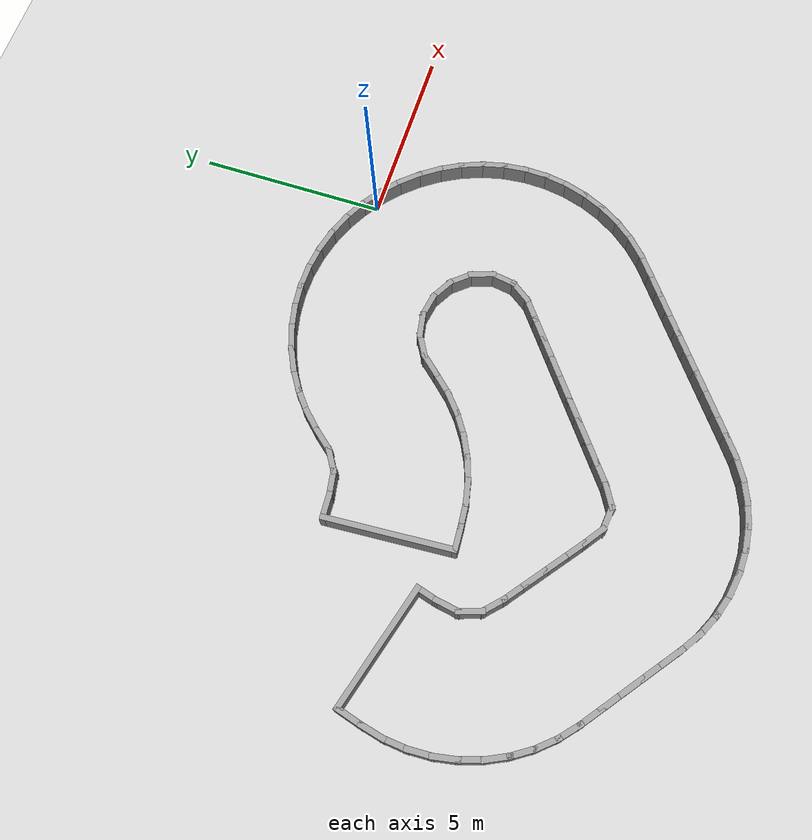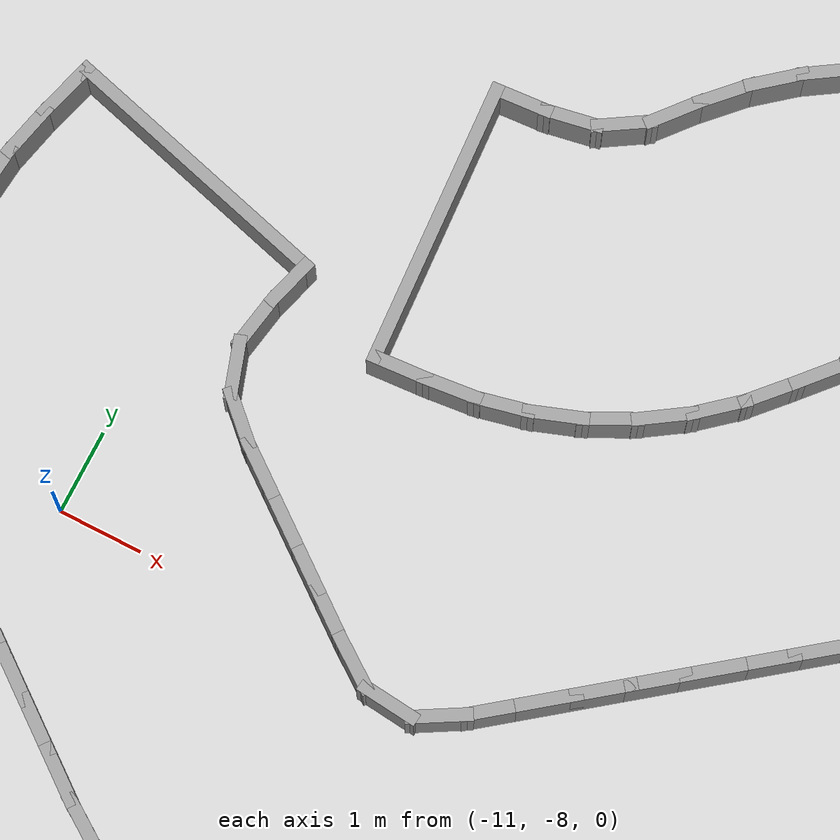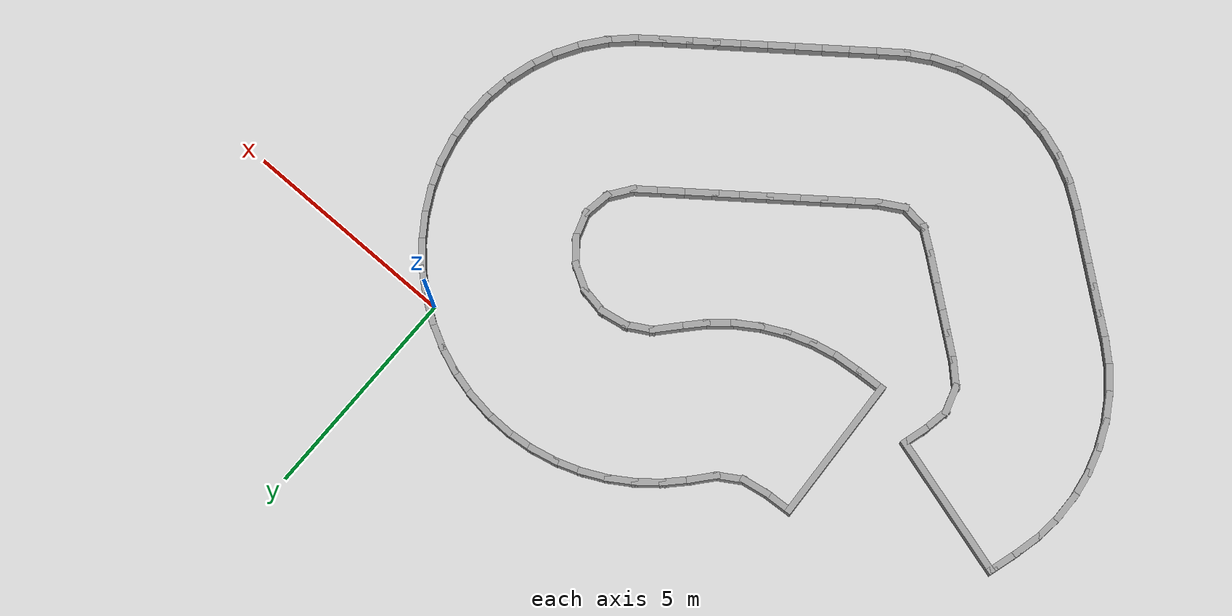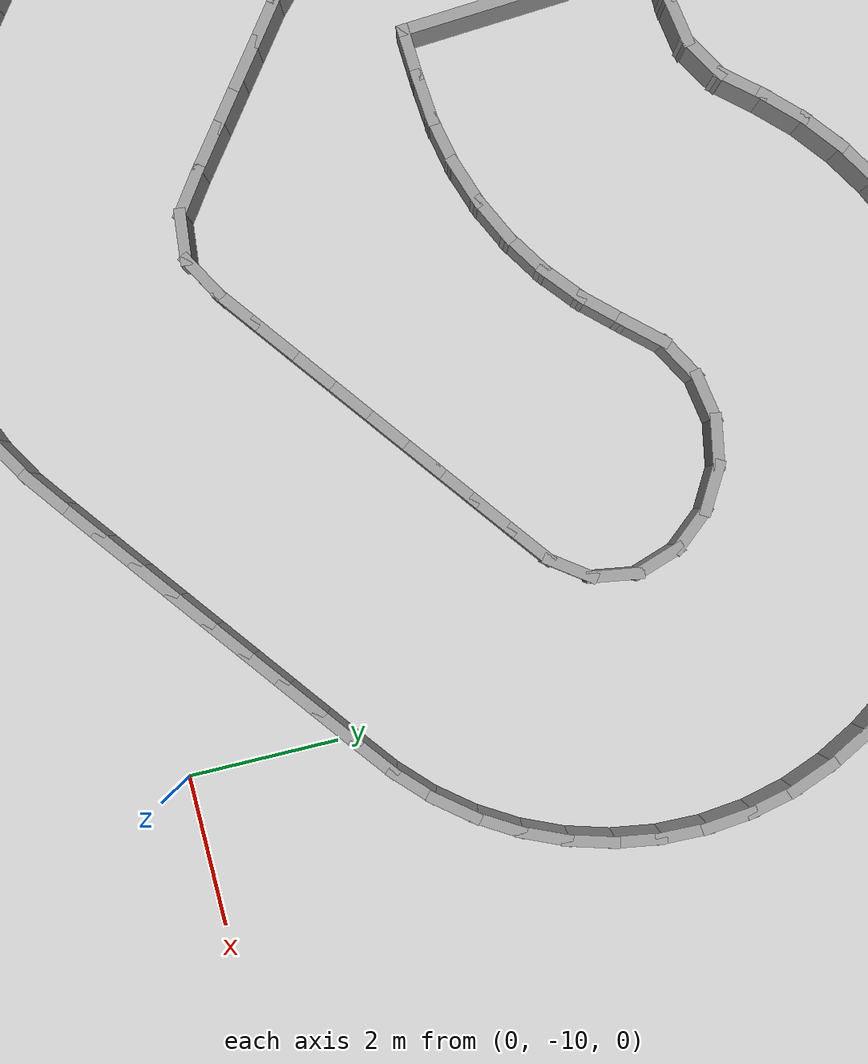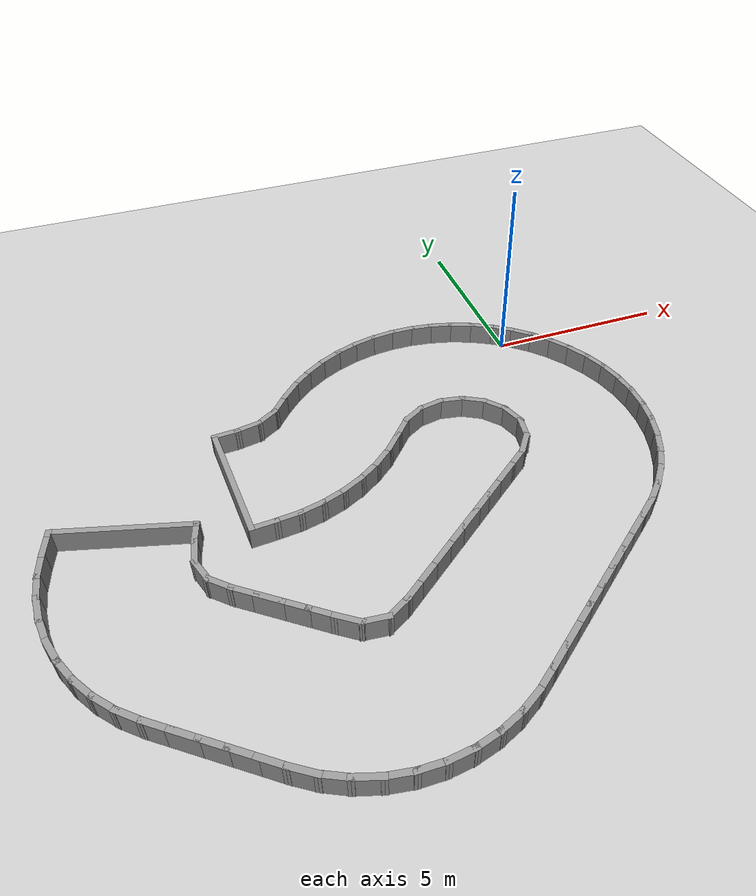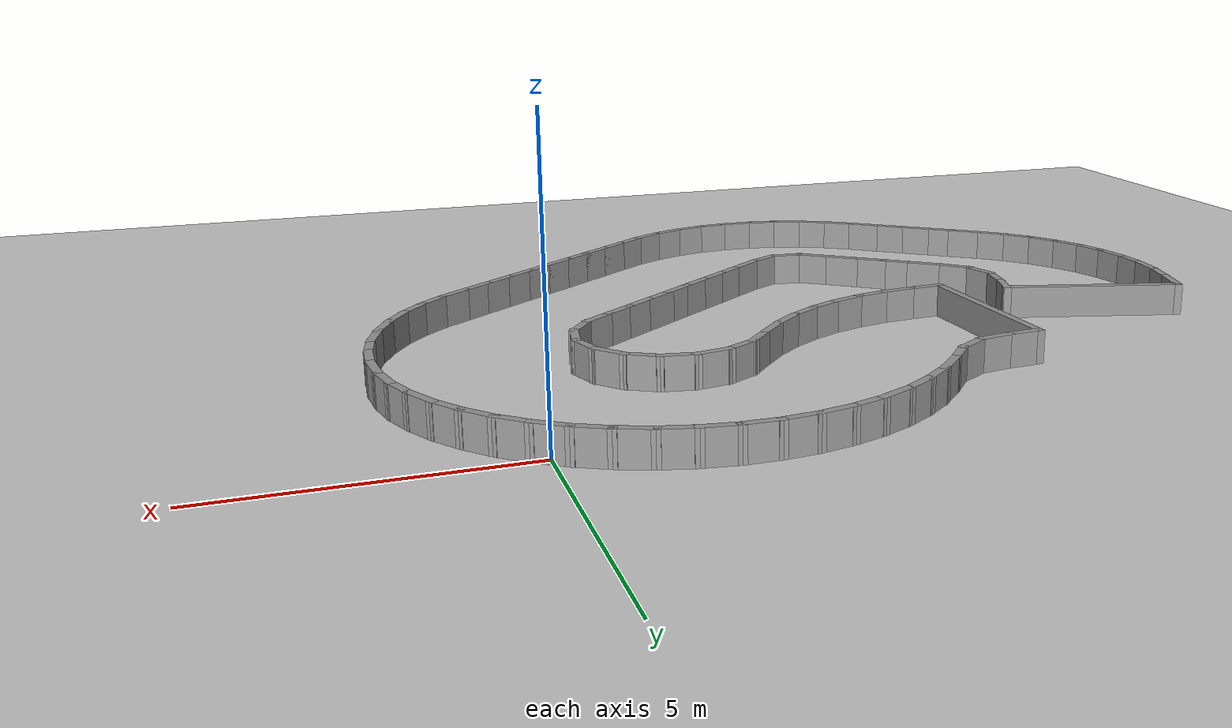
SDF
<?xml version="1.0" ?>
<sdf version='1.7'>
  <world name='default'>
    <plugin name='gazebo_ros_state' filename='libgazebo_ros_state.so'>
      <ros>
        <namespace>/</namespace>
      </ros>
      <update_rate>1000.0</update_rate>
    </plugin>

    <light name='sun' type='directional'>
      <cast_shadows>1</cast_shadows>
      <pose>0 0 10 0 -0 0</pose>
      <diffuse>0.8 0.8 0.8 1</diffuse>
      <specular>0.2 0.2 0.2 1</specular>
      <attenuation>
        <range>1000</range>
        <constant>0.9</constant>
        <linear>0.01</linear>
        <quadratic>0.001</quadratic>
      </attenuation>
      <direction>-0.5 0.1 -0.9</direction>
      <spot>
        <inner_angle>0</inner_angle>
        <outer_angle>0</outer_angle>
        <falloff>0</falloff>
      </spot>
    </light>
    <model name='ground_plane'>
      <static>1</static>
      <link name='link'>
        <collision name='collision'>
          <geometry>
            <plane>
              <normal>0 0 1</normal>
              <size>100 100</size>
            </plane>
          </geometry>
          <surface>
            <friction>
              <ode>
                <mu>100</mu>
                <mu2>50</mu2>
              </ode>
              <torsional>
                <ode/>
              </torsional>
            </friction>
            <contact>
              <ode/>
            </contact>
            <bounce/>
          </surface>
          <max_contacts>10</max_contacts>
        </collision>
        <visual name='visual'>
          <cast_shadows>0</cast_shadows>
          <geometry>
            <plane>
              <normal>0 0 1</normal>
              <size>100 100</size>
            </plane>
          </geometry>
          <material>
            <script>
              <uri>file://media/materials/scripts/gazebo.material</uri>
              <name>Gazebo/Grey</name>
            </script>
          </material>
        </visual>
        <self_collide>0</self_collide>
        <enable_wind>0</enable_wind>
        <kinematic>0</kinematic>
      </link>
    </model>
    <gravity>0 0 -9.8</gravity>
    <magnetic_field>6e-06 2.3e-05 -4.2e-05</magnetic_field>
    <atmosphere type='adiabatic'/>
    <physics type='ode'>
      <max_step_size>0.001</max_step_size>
      <real_time_factor>1</real_time_factor>
      <real_time_update_rate>1000</real_time_update_rate>
    </physics>
    <scene>
      <ambient>0.4 0.4 0.4 1</ambient>
      <background>0.7 0.7 0.7 1</background>
      <shadows>1</shadows>
    </scene>
    <audio>
      <device>default</device>
    </audio>
    <wind/>
    <spherical_coordinates>
      <surface_model>EARTH_WGS84</surface_model>
      <latitude_deg>0</latitude_deg>
      <longitude_deg>0</longitude_deg>
      <elevation>0</elevation>
      <heading_deg>0</heading_deg>
    </spherical_coordinates>
  <model name='rand_turn_00'>
    <pose>0 0 0 0 -0 0</pose>
    <link name='Wall_0'>
      <collision name='Wall_0_Collision'>
        <geometry><box><size>0.7500 0.1500 0.6000</size></box></geometry>
        <pose>0 0 0.3000 0 -0 0</pose>
      </collision>
      <visual name='Wall_0_Visual'>
        <pose>0 0 0.3000 0 -0 0</pose>
        <geometry><box><size>0.7500 0.1500 0.6000</size></box></geometry>
        <material>
          <script>
            <uri>file://media/materials/scripts/gazebo.material</uri>
            <name>Gazebo/Grey</name>
          </script>
          <ambient>1 1 1 1</ambient>
        </material>
      </visual>
      <pose>-8.5441 -1.6204 0 0 -0 0.05897</pose>
    </link>
    <link name='Wall_1'>
      <collision name='Wall_1_Collision'>
        <geometry><box><size>0.7471 0.1500 0.6000</size></box></geometry>
        <pose>0 0 0.3000 0 -0 0</pose>
      </collision>
      <visual name='Wall_1_Visual'>
        <pose>0 0 0.3000 0 -0 0</pose>
        <geometry><box><size>0.7471 0.1500 0.6000</size></box></geometry>
        <material>
          <script>
            <uri>file://media/materials/scripts/gazebo.material</uri>
            <name>Gazebo/Grey</name>
          </script>
          <ambient>1 1 1 1</ambient>
        </material>
      </visual>
      <pose>-7.9503 -1.5525 0 0 -0 0.16929</pose>
    </link>
    <link name='Wall_2'>
      <collision name='Wall_2_Collision'>
        <geometry><box><size>0.7461 0.1500 0.6000</size></box></geometry>
        <pose>0 0 0.3000 0 -0 0</pose>
      </collision>
      <visual name='Wall_2_Visual'>
        <pose>0 0 0.3000 0 -0 0</pose>
        <geometry><box><size>0.7461 0.1500 0.6000</size></box></geometry>
        <material>
          <script>
            <uri>file://media/materials/scripts/gazebo.material</uri>
            <name>Gazebo/Grey</name>
          </script>
          <ambient>1 1 1 1</ambient>
        </material>
      </visual>
      <pose>-7.4023 -1.3457 0 0 -0 0.55249</pose>
    </link>
    <link name='Wall_3'>
      <collision name='Wall_3_Collision'>
        <geometry><box><size>0.7493 0.1500 0.6000</size></box></geometry>
        <pose>0 0 0.3000 0 -0 0</pose>
      </collision>
      <visual name='Wall_3_Visual'>
        <pose>0 0 0.3000 0 -0 0</pose>
        <geometry><box><size>0.7493 0.1500 0.6000</size></box></geometry>
        <material>
          <script>
            <uri>file://media/materials/scripts/gazebo.material</uri>
            <name>Gazebo/Grey</name>
          </script>
          <ambient>1 1 1 1</ambient>
        </material>
      </visual>
      <pose>-6.9553 -0.9603 0 0 -0 0.86976</pose>
    </link>
    <link name='Wall_4'>
      <collision name='Wall_4_Collision'>
        <geometry><box><size>0.7496 0.1500 0.6000</size></box></geometry>
        <pose>0 0 0.3000 0 -0 0</pose>
      </collision>
      <visual name='Wall_4_Visual'>
        <pose>0 0 0.3000 0 -0 0</pose>
        <geometry><box><size>0.7496 0.1500 0.6000</size></box></geometry>
        <material>
          <script>
            <uri>file://media/materials/scripts/gazebo.material</uri>
            <name>Gazebo/Grey</name>
          </script>
          <ambient>1 1 1 1</ambient>
        </material>
      </visual>
      <pose>-6.5543 -0.5152 0 0 -0 0.80530</pose>
    </link>
    <link name='Wall_5'>
      <collision name='Wall_5_Collision'>
        <geometry><box><size>0.7496 0.1500 0.6000</size></box></geometry>
        <pose>0 0 0.3000 0 -0 0</pose>
      </collision>
      <visual name='Wall_5_Visual'>
        <pose>0 0 0.3000 0 -0 0</pose>
        <geometry><box><size>0.7496 0.1500 0.6000</size></box></geometry>
        <material>
          <script>
            <uri>file://media/materials/scripts/gazebo.material</uri>
            <name>Gazebo/Grey</name>
          </script>
          <ambient>1 1 1 1</ambient>
        </material>
      </visual>
      <pose>-6.1148 -0.1088 0 0 -0 0.68736</pose>
    </link>
    <link name='Wall_6'>
      <collision name='Wall_6_Collision'>
        <geometry><box><size>0.7496 0.1500 0.6000</size></box></geometry>
        <pose>0 0 0.3000 0 -0 0</pose>
      </collision>
      <visual name='Wall_6_Visual'>
        <pose>0 0 0.3000 0 -0 0</pose>
        <geometry><box><size>0.7496 0.1500 0.6000</size></box></geometry>
        <material>
          <script>
            <uri>file://media/materials/scripts/gazebo.material</uri>
            <name>Gazebo/Grey</name>
          </script>
          <ambient>1 1 1 1</ambient>
        </material>
      </visual>
      <pose>-5.6306 0.2431 0 0 -0 0.56943</pose>
    </link>
    <link name='Wall_7'>
      <collision name='Wall_7_Collision'>
        <geometry><box><size>0.7496 0.1500 0.6000</size></box></geometry>
        <pose>0 0 0.3000 0 -0 0</pose>
      </collision>
      <visual name='Wall_7_Visual'>
        <pose>0 0 0.3000 0 -0 0</pose>
        <geometry><box><size>0.7496 0.1500 0.6000</size></box></geometry>
        <material>
          <script>
            <uri>file://media/materials/scripts/gazebo.material</uri>
            <name>Gazebo/Grey</name>
          </script>
          <ambient>1 1 1 1</ambient>
        </material>
      </visual>
      <pose>-5.1084 0.5355 0 0 -0 0.45149</pose>
    </link>
    <link name='Wall_8'>
      <collision name='Wall_8_Collision'>
        <geometry><box><size>0.7496 0.1500 0.6000</size></box></geometry>
        <pose>0 0 0.3000 0 -0 0</pose>
      </collision>
      <visual name='Wall_8_Visual'>
        <pose>0 0 0.3000 0 -0 0</pose>
        <geometry><box><size>0.7496 0.1500 0.6000</size></box></geometry>
        <material>
          <script>
            <uri>file://media/materials/scripts/gazebo.material</uri>
            <name>Gazebo/Grey</name>
          </script>
          <ambient>1 1 1 1</ambient>
        </material>
      </visual>
      <pose>-4.5553 0.7645 0 0 -0 0.33355</pose>
    </link>
    <link name='Wall_9'>
      <collision name='Wall_9_Collision'>
        <geometry><box><size>0.7496 0.1500 0.6000</size></box></geometry>
        <pose>0 0 0.3000 0 -0 0</pose>
      </collision>
      <visual name='Wall_9_Visual'>
        <pose>0 0 0.3000 0 -0 0</pose>
        <geometry><box><size>0.7496 0.1500 0.6000</size></box></geometry>
        <material>
          <script>
            <uri>file://media/materials/scripts/gazebo.material</uri>
            <name>Gazebo/Grey</name>
          </script>
          <ambient>1 1 1 1</ambient>
        </material>
      </visual>
      <pose>-3.9792 0.9268 0 0 -0 0.21561</pose>
    </link>
    <link name='Wall_10'>
      <collision name='Wall_10_Collision'>
        <geometry><box><size>0.7496 0.1500 0.6000</size></box></geometry>
        <pose>0 0 0.3000 0 -0 0</pose>
      </collision>
      <visual name='Wall_10_Visual'>
        <pose>0 0 0.3000 0 -0 0</pose>
        <geometry><box><size>0.7496 0.1500 0.6000</size></box></geometry>
        <material>
          <script>
            <uri>file://media/materials/scripts/gazebo.material</uri>
            <name>Gazebo/Grey</name>
          </script>
          <ambient>1 1 1 1</ambient>
        </material>
      </visual>
      <pose>-3.3879 1.0202 0 0 -0 0.09768</pose>
    </link>
    <link name='Wall_11'>
      <collision name='Wall_11_Collision'>
        <geometry><box><size>0.7496 0.1500 0.6000</size></box></geometry>
        <pose>0 0 0.3000 0 -0 0</pose>
      </collision>
      <visual name='Wall_11_Visual'>
        <pose>0 0 0.3000 0 -0 0</pose>
        <geometry><box><size>0.7496 0.1500 0.6000</size></box></geometry>
        <material>
          <script>
            <uri>file://media/materials/scripts/gazebo.material</uri>
            <name>Gazebo/Grey</name>
          </script>
          <ambient>1 1 1 1</ambient>
        </material>
      </visual>
      <pose>-2.7898 1.0434 0 0 -0 -0.02026</pose>
    </link>
    <link name='Wall_12'>
      <collision name='Wall_12_Collision'>
        <geometry><box><size>0.7496 0.1500 0.6000</size></box></geometry>
        <pose>0 0 0.3000 0 -0 0</pose>
      </collision>
      <visual name='Wall_12_Visual'>
        <pose>0 0 0.3000 0 -0 0</pose>
        <geometry><box><size>0.7496 0.1500 0.6000</size></box></geometry>
        <material>
          <script>
            <uri>file://media/materials/scripts/gazebo.material</uri>
            <name>Gazebo/Grey</name>
          </script>
          <ambient>1 1 1 1</ambient>
        </material>
      </visual>
      <pose>-2.1931 0.9960 0 0 -0 -0.13820</pose>
    </link>
    <link name='Wall_13'>
      <collision name='Wall_13_Collision'>
        <geometry><box><size>0.7496 0.1500 0.6000</size></box></geometry>
        <pose>0 0 0.3000 0 -0 0</pose>
      </collision>
      <visual name='Wall_13_Visual'>
        <pose>0 0 0.3000 0 -0 0</pose>
        <geometry><box><size>0.7496 0.1500 0.6000</size></box></geometry>
        <material>
          <script>
            <uri>file://media/materials/scripts/gazebo.material</uri>
            <name>Gazebo/Grey</name>
          </script>
          <ambient>1 1 1 1</ambient>
        </material>
      </visual>
      <pose>-1.6061 0.8787 0 0 -0 -0.25614</pose>
    </link>
    <link name='Wall_14'>
      <collision name='Wall_14_Collision'>
        <geometry><box><size>0.7496 0.1500 0.6000</size></box></geometry>
        <pose>0 0 0.3000 0 -0 0</pose>
      </collision>
      <visual name='Wall_14_Visual'>
        <pose>0 0 0.3000 0 -0 0</pose>
        <geometry><box><size>0.7496 0.1500 0.6000</size></box></geometry>
        <material>
          <script>
            <uri>file://media/materials/scripts/gazebo.material</uri>
            <name>Gazebo/Grey</name>
          </script>
          <ambient>1 1 1 1</ambient>
        </material>
      </visual>
      <pose>-1.0370 0.6932 0 0 -0 -0.37407</pose>
    </link>
    <link name='Wall_15'>
      <collision name='Wall_15_Collision'>
        <geometry><box><size>0.7496 0.1500 0.6000</size></box></geometry>
        <pose>0 0 0.3000 0 -0 0</pose>
      </collision>
      <visual name='Wall_15_Visual'>
        <pose>0 0 0.3000 0 -0 0</pose>
        <geometry><box><size>0.7496 0.1500 0.6000</size></box></geometry>
        <material>
          <script>
            <uri>file://media/materials/scripts/gazebo.material</uri>
            <name>Gazebo/Grey</name>
          </script>
          <ambient>1 1 1 1</ambient>
        </material>
      </visual>
      <pose>-0.4937 0.4420 0 0 -0 -0.49201</pose>
    </link>
    <link name='Wall_16'>
      <collision name='Wall_16_Collision'>
        <geometry><box><size>0.7496 0.1500 0.6000</size></box></geometry>
        <pose>0 0 0.3000 0 -0 0</pose>
      </collision>
      <visual name='Wall_16_Visual'>
        <pose>0 0 0.3000 0 -0 0</pose>
        <geometry><box><size>0.7496 0.1500 0.6000</size></box></geometry>
        <material>
          <script>
            <uri>file://media/materials/scripts/gazebo.material</uri>
            <name>Gazebo/Grey</name>
          </script>
          <ambient>1 1 1 1</ambient>
        </material>
      </visual>
      <pose>0.0163 0.1287 0 0 -0 -0.60995</pose>
    </link>
    <link name='Wall_17'>
      <collision name='Wall_17_Collision'>
        <geometry><box><size>0.7496 0.1500 0.6000</size></box></geometry>
        <pose>0 0 0.3000 0 -0 0</pose>
      </collision>
      <visual name='Wall_17_Visual'>
        <pose>0 0 0.3000 0 -0 0</pose>
        <geometry><box><size>0.7496 0.1500 0.6000</size></box></geometry>
        <material>
          <script>
            <uri>file://media/materials/scripts/gazebo.material</uri>
            <name>Gazebo/Grey</name>
          </script>
          <ambient>1 1 1 1</ambient>
        </material>
      </visual>
      <pose>0.4859 -0.2426 0 0 -0 -0.72788</pose>
    </link>
    <link name='Wall_18'>
      <collision name='Wall_18_Collision'>
        <geometry><box><size>0.7496 0.1500 0.6000</size></box></geometry>
        <pose>0 0 0.3000 0 -0 0</pose>
      </collision>
      <visual name='Wall_18_Visual'>
        <pose>0 0 0.3000 0 -0 0</pose>
        <geometry><box><size>0.7496 0.1500 0.6000</size></box></geometry>
        <material>
          <script>
            <uri>file://media/materials/scripts/gazebo.material</uri>
            <name>Gazebo/Grey</name>
          </script>
          <ambient>1 1 1 1</ambient>
        </material>
      </visual>
      <pose>0.9086 -0.6664 0 0 -0 -0.84582</pose>
    </link>
    <link name='Wall_19'>
      <collision name='Wall_19_Collision'>
        <geometry><box><size>0.7496 0.1500 0.6000</size></box></geometry>
        <pose>0 0 0.3000 0 -0 0</pose>
      </collision>
      <visual name='Wall_19_Visual'>
        <pose>0 0 0.3000 0 -0 0</pose>
        <geometry><box><size>0.7496 0.1500 0.6000</size></box></geometry>
        <material>
          <script>
            <uri>file://media/materials/scripts/gazebo.material</uri>
            <name>Gazebo/Grey</name>
          </script>
          <ambient>1 1 1 1</ambient>
        </material>
      </visual>
      <pose>1.2784 -1.1371 0 0 -0 -0.96376</pose>
    </link>
    <link name='Wall_20'>
      <collision name='Wall_20_Collision'>
        <geometry><box><size>0.7496 0.1500 0.6000</size></box></geometry>
        <pose>0 0 0.3000 0 -0 0</pose>
      </collision>
      <visual name='Wall_20_Visual'>
        <pose>0 0 0.3000 0 -0 0</pose>
        <geometry><box><size>0.7496 0.1500 0.6000</size></box></geometry>
        <material>
          <script>
            <uri>file://media/materials/scripts/gazebo.material</uri>
            <name>Gazebo/Grey</name>
          </script>
          <ambient>1 1 1 1</ambient>
        </material>
      </visual>
      <pose>1.5903 -1.6480 0 0 -0 -1.08170</pose>
    </link>
    <link name='Wall_21'>
      <collision name='Wall_21_Collision'>
        <geometry><box><size>0.7495 0.1500 0.6000</size></box></geometry>
        <pose>0 0 0.3000 0 -0 0</pose>
      </collision>
      <visual name='Wall_21_Visual'>
        <pose>0 0 0.3000 0 -0 0</pose>
        <geometry><box><size>0.7495 0.1500 0.6000</size></box></geometry>
        <material>
          <script>
            <uri>file://media/materials/scripts/gazebo.material</uri>
            <name>Gazebo/Grey</name>
          </script>
          <ambient>1 1 1 1</ambient>
        </material>
      </visual>
      <pose>1.8387 -2.1925 0 0 -0 -1.20371</pose>
    </link>
    <link name='Wall_22'>
      <collision name='Wall_22_Collision'>
        <geometry><box><size>0.7495 0.1500 0.6000</size></box></geometry>
        <pose>0 0 0.3000 0 -0 0</pose>
      </collision>
      <visual name='Wall_22_Visual'>
        <pose>0 0 0.3000 0 -0 0</pose>
        <geometry><box><size>0.7495 0.1500 0.6000</size></box></geometry>
        <material>
          <script>
            <uri>file://media/materials/scripts/gazebo.material</uri>
            <name>Gazebo/Grey</name>
          </script>
          <ambient>1 1 1 1</ambient>
        </material>
      </visual>
      <pose>2.0146 -2.7641 0 0 -0 -1.34086</pose>
    </link>
    <link name='Wall_23'>
      <collision name='Wall_23_Collision'>
        <geometry><box><size>0.7495 0.1500 0.6000</size></box></geometry>
        <pose>0 0 0.3000 0 -0 0</pose>
      </collision>
      <visual name='Wall_23_Visual'>
        <pose>0 0 0.3000 0 -0 0</pose>
        <geometry><box><size>0.7495 0.1500 0.6000</size></box></geometry>
        <material>
          <script>
            <uri>file://media/materials/scripts/gazebo.material</uri>
            <name>Gazebo/Grey</name>
          </script>
          <ambient>1 1 1 1</ambient>
        </material>
      </visual>
      <pose>2.1131 -3.3543 0 0 -0 -1.47015</pose>
    </link>
    <link name='Wall_24'>
      <collision name='Wall_24_Collision'>
        <geometry><box><size>0.7496 0.1500 0.6000</size></box></geometry>
        <pose>0 0 0.3000 0 -0 0</pose>
      </collision>
      <visual name='Wall_24_Visual'>
        <pose>0 0 0.3000 0 -0 0</pose>
        <geometry><box><size>0.7496 0.1500 0.6000</size></box></geometry>
        <material>
          <script>
            <uri>file://media/materials/scripts/gazebo.material</uri>
            <name>Gazebo/Grey</name>
          </script>
          <ambient>1 1 1 1</ambient>
        </material>
      </visual>
      <pose>2.1347 -3.9522 0 0 -0 -1.59920</pose>
    </link>
    <link name='Wall_25'>
      <collision name='Wall_25_Collision'>
        <geometry><box><size>0.7496 0.1500 0.6000</size></box></geometry>
        <pose>0 0 0.3000 0 -0 0</pose>
      </collision>
      <visual name='Wall_25_Visual'>
        <pose>0 0 0.3000 0 -0 0</pose>
        <geometry><box><size>0.7496 0.1500 0.6000</size></box></geometry>
        <material>
          <script>
            <uri>file://media/materials/scripts/gazebo.material</uri>
            <name>Gazebo/Grey</name>
          </script>
          <ambient>1 1 1 1</ambient>
        </material>
      </visual>
      <pose>2.0789 -4.5479 0 0 -0 -1.72908</pose>
    </link>
    <link name='Wall_26'>
      <collision name='Wall_26_Collision'>
        <geometry><box><size>0.7496 0.1500 0.6000</size></box></geometry>
        <pose>0 0 0.3000 0 -0 0</pose>
      </collision>
      <visual name='Wall_26_Visual'>
        <pose>0 0 0.3000 0 -0 0</pose>
        <geometry><box><size>0.7496 0.1500 0.6000</size></box></geometry>
        <material>
          <script>
            <uri>file://media/materials/scripts/gazebo.material</uri>
            <name>Gazebo/Grey</name>
          </script>
          <ambient>1 1 1 1</ambient>
        </material>
      </visual>
      <pose>1.9465 -5.1314 0 0 -0 -1.85879</pose>
    </link>
    <link name='Wall_27'>
      <collision name='Wall_27_Collision'>
        <geometry><box><size>0.7495 0.1500 0.6000</size></box></geometry>
        <pose>0 0 0.3000 0 -0 0</pose>
      </collision>
      <visual name='Wall_27_Visual'>
        <pose>0 0 0.3000 0 -0 0</pose>
        <geometry><box><size>0.7495 0.1500 0.6000</size></box></geometry>
        <material>
          <script>
            <uri>file://media/materials/scripts/gazebo.material</uri>
            <name>Gazebo/Grey</name>
          </script>
          <ambient>1 1 1 1</ambient>
        </material>
      </visual>
      <pose>1.7400 -5.6929 0 0 -0 -1.98783</pose>
    </link>
    <link name='Wall_28'>
      <collision name='Wall_28_Collision'>
        <geometry><box><size>0.7495 0.1500 0.6000</size></box></geometry>
        <pose>0 0 0.3000 0 -0 0</pose>
      </collision>
      <visual name='Wall_28_Visual'>
        <pose>0 0 0.3000 0 -0 0</pose>
        <geometry><box><size>0.7495 0.1500 0.6000</size></box></geometry>
        <material>
          <script>
            <uri>file://media/materials/scripts/gazebo.material</uri>
            <name>Gazebo/Grey</name>
          </script>
          <ambient>1 1 1 1</ambient>
        </material>
      </visual>
      <pose>1.4629 -6.2231 0 0 -0 -2.11688</pose>
    </link>
    <link name='Wall_29'>
      <collision name='Wall_29_Collision'>
        <geometry><box><size>0.7495 0.1500 0.6000</size></box></geometry>
        <pose>0 0 0.3000 0 -0 0</pose>
      </collision>
      <visual name='Wall_29_Visual'>
        <pose>0 0 0.3000 0 -0 0</pose>
        <geometry><box><size>0.7495 0.1500 0.6000</size></box></geometry>
        <material>
          <script>
            <uri>file://media/materials/scripts/gazebo.material</uri>
            <name>Gazebo/Grey</name>
          </script>
          <ambient>1 1 1 1</ambient>
        </material>
      </visual>
      <pose>1.1198 -6.7133 0 0 -0 -2.24592</pose>
    </link>
    <link name='Wall_30'>
      <collision name='Wall_30_Collision'>
        <geometry><box><size>0.7496 0.1500 0.6000</size></box></geometry>
        <pose>0 0 0.3000 0 -0 0</pose>
      </collision>
      <visual name='Wall_30_Visual'>
        <pose>0 0 0.3000 0 -0 0</pose>
        <geometry><box><size>0.7496 0.1500 0.6000</size></box></geometry>
        <material>
          <script>
            <uri>file://media/materials/scripts/gazebo.material</uri>
            <name>Gazebo/Grey</name>
          </script>
          <ambient>1 1 1 1</ambient>
        </material>
      </visual>
      <pose>0.7165 -7.1553 0 0 -0 -2.37497</pose>
    </link>
    <link name='Wall_31'>
      <collision name='Wall_31_Collision'>
        <geometry><box><size>0.7499 0.1500 0.6000</size></box></geometry>
        <pose>0 0 0.3000 0 -0 0</pose>
      </collision>
      <visual name='Wall_31_Visual'>
        <pose>0 0 0.3000 0 -0 0</pose>
        <geometry><box><size>0.7499 0.1500 0.6000</size></box></geometry>
        <material>
          <script>
            <uri>file://media/materials/scripts/gazebo.material</uri>
            <name>Gazebo/Grey</name>
          </script>
          <ambient>1 1 1 1</ambient>
        </material>
      </visual>
      <pose>0.2639 -7.5475 0 0 -0 -2.48004</pose>
    </link>
    <link name='Wall_32'>
      <collision name='Wall_32_Collision'>
        <geometry><box><size>0.7500 0.1500 0.6000</size></box></geometry>
        <pose>0 0 0.3000 0 -0 0</pose>
      </collision>
      <visual name='Wall_32_Visual'>
        <pose>0 0 0.3000 0 -0 0</pose>
        <geometry><box><size>0.7500 0.1500 0.6000</size></box></geometry>
        <material>
          <script>
            <uri>file://media/materials/scripts/gazebo.material</uri>
            <name>Gazebo/Grey</name>
          </script>
          <ambient>1 1 1 1</ambient>
        </material>
      </visual>
      <pose>-0.2110 -7.9140 0 0 -0 -2.48869</pose>
    </link>
    <link name='Wall_33'>
      <collision name='Wall_33_Collision'>
        <geometry><box><size>0.7500 0.1500 0.6000</size></box></geometry>
        <pose>0 0 0.3000 0 -0 0</pose>
      </collision>
      <visual name='Wall_33_Visual'>
        <pose>0 0 0.3000 0 -0 0</pose>
        <geometry><box><size>0.7500 0.1500 0.6000</size></box></geometry>
        <material>
          <script>
            <uri>file://media/materials/scripts/gazebo.material</uri>
            <name>Gazebo/Grey</name>
          </script>
          <ambient>1 1 1 1</ambient>
        </material>
      </visual>
      <pose>-0.6876 -8.2785 0 0 -0 -2.48869</pose>
    </link>
    <link name='Wall_34'>
      <collision name='Wall_34_Collision'>
        <geometry><box><size>0.7500 0.1500 0.6000</size></box></geometry>
        <pose>0 0 0.3000 0 -0 0</pose>
      </collision>
      <visual name='Wall_34_Visual'>
        <pose>0 0 0.3000 0 -0 0</pose>
        <geometry><box><size>0.7500 0.1500 0.6000</size></box></geometry>
        <material>
          <script>
            <uri>file://media/materials/scripts/gazebo.material</uri>
            <name>Gazebo/Grey</name>
          </script>
          <ambient>1 1 1 1</ambient>
        </material>
      </visual>
      <pose>-1.1642 -8.6430 0 0 -0 -2.48869</pose>
    </link>
    <link name='Wall_35'>
      <collision name='Wall_35_Collision'>
        <geometry><box><size>0.7500 0.1500 0.6000</size></box></geometry>
        <pose>0 0 0.3000 0 -0 0</pose>
      </collision>
      <visual name='Wall_35_Visual'>
        <pose>0 0 0.3000 0 -0 0</pose>
        <geometry><box><size>0.7500 0.1500 0.6000</size></box></geometry>
        <material>
          <script>
            <uri>file://media/materials/scripts/gazebo.material</uri>
            <name>Gazebo/Grey</name>
          </script>
          <ambient>1 1 1 1</ambient>
        </material>
      </visual>
      <pose>-1.6408 -9.0075 0 0 -0 -2.48869</pose>
    </link>
    <link name='Wall_36'>
      <collision name='Wall_36_Collision'>
        <geometry><box><size>0.7500 0.1500 0.6000</size></box></geometry>
        <pose>0 0 0.3000 0 -0 0</pose>
      </collision>
      <visual name='Wall_36_Visual'>
        <pose>0 0 0.3000 0 -0 0</pose>
        <geometry><box><size>0.7500 0.1500 0.6000</size></box></geometry>
        <material>
          <script>
            <uri>file://media/materials/scripts/gazebo.material</uri>
            <name>Gazebo/Grey</name>
          </script>
          <ambient>1 1 1 1</ambient>
        </material>
      </visual>
      <pose>-2.1174 -9.3720 0 0 -0 -2.48869</pose>
    </link>
    <link name='Wall_37'>
      <collision name='Wall_37_Collision'>
        <geometry><box><size>0.7500 0.1500 0.6000</size></box></geometry>
        <pose>0 0 0.3000 0 -0 0</pose>
      </collision>
      <visual name='Wall_37_Visual'>
        <pose>0 0 0.3000 0 -0 0</pose>
        <geometry><box><size>0.7500 0.1500 0.6000</size></box></geometry>
        <material>
          <script>
            <uri>file://media/materials/scripts/gazebo.material</uri>
            <name>Gazebo/Grey</name>
          </script>
          <ambient>1 1 1 1</ambient>
        </material>
      </visual>
      <pose>-2.5940 -9.7365 0 0 -0 -2.48869</pose>
    </link>
    <link name='Wall_38'>
      <collision name='Wall_38_Collision'>
        <geometry><box><size>0.7500 0.1500 0.6000</size></box></geometry>
        <pose>0 0 0.3000 0 -0 0</pose>
      </collision>
      <visual name='Wall_38_Visual'>
        <pose>0 0 0.3000 0 -0 0</pose>
        <geometry><box><size>0.7500 0.1500 0.6000</size></box></geometry>
        <material>
          <script>
            <uri>file://media/materials/scripts/gazebo.material</uri>
            <name>Gazebo/Grey</name>
          </script>
          <ambient>1 1 1 1</ambient>
        </material>
      </visual>
      <pose>-3.0706 -10.1010 0 0 -0 -2.48869</pose>
    </link>
    <link name='Wall_39'>
      <collision name='Wall_39_Collision'>
        <geometry><box><size>0.7500 0.1500 0.6000</size></box></geometry>
        <pose>0 0 0.3000 0 -0 0</pose>
      </collision>
      <visual name='Wall_39_Visual'>
        <pose>0 0 0.3000 0 -0 0</pose>
        <geometry><box><size>0.7500 0.1500 0.6000</size></box></geometry>
        <material>
          <script>
            <uri>file://media/materials/scripts/gazebo.material</uri>
            <name>Gazebo/Grey</name>
          </script>
          <ambient>1 1 1 1</ambient>
        </material>
      </visual>
      <pose>-3.5472 -10.4655 0 0 -0 -2.48869</pose>
    </link>
    <link name='Wall_40'>
      <collision name='Wall_40_Collision'>
        <geometry><box><size>0.7499 0.1500 0.6000</size></box></geometry>
        <pose>0 0 0.3000 0 -0 0</pose>
      </collision>
      <visual name='Wall_40_Visual'>
        <pose>0 0 0.3000 0 -0 0</pose>
        <geometry><box><size>0.7499 0.1500 0.6000</size></box></geometry>
        <material>
          <script>
            <uri>file://media/materials/scripts/gazebo.material</uri>
            <name>Gazebo/Grey</name>
          </script>
          <ambient>1 1 1 1</ambient>
        </material>
      </visual>
      <pose>-4.0258 -10.8273 0 0 -0 -2.49975</pose>
    </link>
    <link name='Wall_41'>
      <collision name='Wall_41_Collision'>
        <geometry><box><size>0.7495 0.1500 0.6000</size></box></geometry>
        <pose>0 0 0.3000 0 -0 0</pose>
      </collision>
      <visual name='Wall_41_Visual'>
        <pose>0 0 0.3000 0 -0 0</pose>
        <geometry><box><size>0.7495 0.1500 0.6000</size></box></geometry>
        <material>
          <script>
            <uri>file://media/materials/scripts/gazebo.material</uri>
            <name>Gazebo/Grey</name>
          </script>
          <ambient>1 1 1 1</ambient>
        </material>
      </visual>
      <pose>-4.5245 -11.1586 0 0 -0 -2.61095</pose>
    </link>
    <link name='Wall_42'>
      <collision name='Wall_42_Collision'>
        <geometry><box><size>0.7495 0.1500 0.6000</size></box></geometry>
        <pose>0 0 0.3000 0 -0 0</pose>
      </collision>
      <visual name='Wall_42_Visual'>
        <pose>0 0 0.3000 0 -0 0</pose>
        <geometry><box><size>0.7495 0.1500 0.6000</size></box></geometry>
        <material>
          <script>
            <uri>file://media/materials/scripts/gazebo.material</uri>
            <name>Gazebo/Grey</name>
          </script>
          <ambient>1 1 1 1</ambient>
        </material>
      </visual>
      <pose>-5.0606 -11.4234 0 0 -0 -2.75458</pose>
    </link>
    <link name='Wall_43'>
      <collision name='Wall_43_Collision'>
        <geometry><box><size>0.7494 0.1500 0.6000</size></box></geometry>
        <pose>0 0 0.3000 0 -0 0</pose>
      </collision>
      <visual name='Wall_43_Visual'>
        <pose>0 0 0.3000 0 -0 0</pose>
        <geometry><box><size>0.7494 0.1500 0.6000</size></box></geometry>
        <material>
          <script>
            <uri>file://media/materials/scripts/gazebo.material</uri>
            <name>Gazebo/Grey</name>
          </script>
          <ambient>1 1 1 1</ambient>
        </material>
      </visual>
      <pose>-5.6288 -11.6099 0 0 -0 -2.89441</pose>
    </link>
    <link name='Wall_44'>
      <collision name='Wall_44_Collision'>
        <geometry><box><size>0.7495 0.1500 0.6000</size></box></geometry>
        <pose>0 0 0.3000 0 -0 0</pose>
      </collision>
      <visual name='Wall_44_Visual'>
        <pose>0 0 0.3000 0 -0 0</pose>
        <geometry><box><size>0.7495 0.1500 0.6000</size></box></geometry>
        <material>
          <script>
            <uri>file://media/materials/scripts/gazebo.material</uri>
            <name>Gazebo/Grey</name>
          </script>
          <ambient>1 1 1 1</ambient>
        </material>
      </visual>
      <pose>-6.2175 -11.7149 0 0 -0 -3.03569</pose>
    </link>
    <link name='Wall_45'>
      <collision name='Wall_45_Collision'>
        <geometry><box><size>0.7495 0.1500 0.6000</size></box></geometry>
        <pose>0 0 0.3000 0 -0 0</pose>
      </collision>
      <visual name='Wall_45_Visual'>
        <pose>0 0 0.3000 0 -0 0</pose>
        <geometry><box><size>0.7495 0.1500 0.6000</size></box></geometry>
        <material>
          <script>
            <uri>file://media/materials/scripts/gazebo.material</uri>
            <name>Gazebo/Grey</name>
          </script>
          <ambient>1 1 1 1</ambient>
        </material>
      </visual>
      <pose>-6.8151 -11.7357 0 0 -0 3.10511</pose>
    </link>
    <link name='Wall_46'>
      <collision name='Wall_46_Collision'>
        <geometry><box><size>0.7495 0.1500 0.6000</size></box></geometry>
        <pose>0 0 0.3000 0 -0 0</pose>
      </collision>
      <visual name='Wall_46_Visual'>
        <pose>0 0 0.3000 0 -0 0</pose>
        <geometry><box><size>0.7495 0.1500 0.6000</size></box></geometry>
        <material>
          <script>
            <uri>file://media/materials/scripts/gazebo.material</uri>
            <name>Gazebo/Grey</name>
          </script>
          <ambient>1 1 1 1</ambient>
        </material>
      </visual>
      <pose>-7.4097 -11.6722 0 0 -0 2.96528</pose>
    </link>
    <link name='Wall_47'>
      <collision name='Wall_47_Collision'>
        <geometry><box><size>0.7495 0.1500 0.6000</size></box></geometry>
        <pose>0 0 0.3000 0 -0 0</pose>
      </collision>
      <visual name='Wall_47_Visual'>
        <pose>0 0 0.3000 0 -0 0</pose>
        <geometry><box><size>0.7495 0.1500 0.6000</size></box></geometry>
        <material>
          <script>
            <uri>file://media/materials/scripts/gazebo.material</uri>
            <name>Gazebo/Grey</name>
          </script>
          <ambient>1 1 1 1</ambient>
        </material>
      </visual>
      <pose>-7.9894 -11.5256 0 0 -0 2.82276</pose>
    </link>
    <link name='Wall_48'>
      <collision name='Wall_48_Collision'>
        <geometry><box><size>0.7494 0.1500 0.6000</size></box></geometry>
        <pose>0 0 0.3000 0 -0 0</pose>
      </collision>
      <visual name='Wall_48_Visual'>
        <pose>0 0 0.3000 0 -0 0</pose>
        <geometry><box><size>0.7494 0.1500 0.6000</size></box></geometry>
        <material>
          <script>
            <uri>file://media/materials/scripts/gazebo.material</uri>
            <name>Gazebo/Grey</name>
          </script>
          <ambient>1 1 1 1</ambient>
        </material>
      </visual>
      <pose>-8.5426 -11.2986 0 0 -0 2.68162</pose>
    </link>
    <link name='Wall_49'>
      <collision name='Wall_49_Collision'>
        <geometry><box><size>0.7495 0.1500 0.6000</size></box></geometry>
        <pose>0 0 0.3000 0 -0 0</pose>
      </collision>
      <visual name='Wall_49_Visual'>
        <pose>0 0 0.3000 0 -0 0</pose>
        <geometry><box><size>0.7495 0.1500 0.6000</size></box></geometry>
        <material>
          <script>
            <uri>file://media/materials/scripts/gazebo.material</uri>
            <name>Gazebo/Grey</name>
          </script>
          <ambient>1 1 1 1</ambient>
        </material>
      </visual>
      <pose>-9.0584 -10.9962 0 0 -0 2.54093</pose>
    </link>
    <link name='Wall_50'>
      <collision name='Wall_50_Collision'>
        <geometry><box><size>0.7500 0.1500 0.6000</size></box></geometry>
        <pose>0 0 0.3000 0 -0 0</pose>
      </collision>
      <visual name='Wall_50_Visual'>
        <pose>0 0 0.3000 0 -0 0</pose>
        <geometry><box><size>0.7500 0.1500 0.6000</size></box></geometry>
        <material>
          <script>
            <uri>file://media/materials/scripts/gazebo.material</uri>
            <name>Gazebo/Grey</name>
          </script>
          <ambient>1 1 1 1</ambient>
        </material>
      </visual>
      <pose>-9.5429 -10.6431 0 0 -0 2.48282</pose>
    </link>
    <link name='Wall_51'>
      <collision name='Wall_51_Collision'>
        <geometry><box><size>0.7500 0.1500 0.6000</size></box></geometry>
        <pose>0 0 0.3000 0 -0 0</pose>
      </collision>
      <visual name='Wall_51_Visual'>
        <pose>0 0 0.3000 0 -0 0</pose>
        <geometry><box><size>0.7500 0.1500 0.6000</size></box></geometry>
        <material>
          <script>
            <uri>file://media/materials/scripts/gazebo.material</uri>
            <name>Gazebo/Grey</name>
          </script>
          <ambient>1 1 1 1</ambient>
        </material>
      </visual>
      <pose>-10.0174 -10.2758 0 0 -0 2.48282</pose>
    </link>
    <link name='Wall_52'>
      <collision name='Wall_52_Collision'>
        <geometry><box><size>0.7500 0.1500 0.6000</size></box></geometry>
        <pose>0 0 0.3000 0 -0 0</pose>
      </collision>
      <visual name='Wall_52_Visual'>
        <pose>0 0 0.3000 0 -0 0</pose>
        <geometry><box><size>0.7500 0.1500 0.6000</size></box></geometry>
        <material>
          <script>
            <uri>file://media/materials/scripts/gazebo.material</uri>
            <name>Gazebo/Grey</name>
          </script>
          <ambient>1 1 1 1</ambient>
        </material>
      </visual>
      <pose>-10.4918 -9.9086 0 0 -0 2.48282</pose>
    </link>
    <link name='Wall_53'>
      <collision name='Wall_53_Collision'>
        <geometry><box><size>0.7500 0.1500 0.6000</size></box></geometry>
        <pose>0 0 0.3000 0 -0 0</pose>
      </collision>
      <visual name='Wall_53_Visual'>
        <pose>0 0 0.3000 0 -0 0</pose>
        <geometry><box><size>0.7500 0.1500 0.6000</size></box></geometry>
        <material>
          <script>
            <uri>file://media/materials/scripts/gazebo.material</uri>
            <name>Gazebo/Grey</name>
          </script>
          <ambient>1 1 1 1</ambient>
        </material>
      </visual>
      <pose>-10.9663 -9.5413 0 0 -0 2.48282</pose>
    </link>
    <link name='Wall_54'>
      <collision name='Wall_54_Collision'>
        <geometry><box><size>0.7500 0.1500 0.6000</size></box></geometry>
        <pose>0 0 0.3000 0 -0 0</pose>
      </collision>
      <visual name='Wall_54_Visual'>
        <pose>0 0 0.3000 0 -0 0</pose>
        <geometry><box><size>0.7500 0.1500 0.6000</size></box></geometry>
        <material>
          <script>
            <uri>file://media/materials/scripts/gazebo.material</uri>
            <name>Gazebo/Grey</name>
          </script>
          <ambient>1 1 1 1</ambient>
        </material>
      </visual>
      <pose>-11.4406 -9.1739 0 0 -0 2.48247</pose>
    </link>
    <link name='Wall_55'>
      <collision name='Wall_55_Collision'>
        <geometry><box><size>0.7496 0.1500 0.6000</size></box></geometry>
        <pose>0 0 0.3000 0 -0 0</pose>
      </collision>
      <visual name='Wall_55_Visual'>
        <pose>0 0 0.3000 0 -0 0</pose>
        <geometry><box><size>0.7496 0.1500 0.6000</size></box></geometry>
        <material>
          <script>
            <uri>file://media/materials/scripts/gazebo.material</uri>
            <name>Gazebo/Grey</name>
          </script>
          <ambient>1 1 1 1</ambient>
        </material>
      </visual>
      <pose>-11.9011 -8.7901 0 0 -0 2.41105</pose>
    </link>
    <link name='Wall_56'>
      <collision name='Wall_56_Collision'>
        <geometry><box><size>0.7495 0.1500 0.6000</size></box></geometry>
        <pose>0 0 0.3000 0 -0 0</pose>
      </collision>
      <visual name='Wall_56_Visual'>
        <pose>0 0 0.3000 0 -0 0</pose>
        <geometry><box><size>0.7495 0.1500 0.6000</size></box></geometry>
        <material>
          <script>
            <uri>file://media/materials/scripts/gazebo.material</uri>
            <name>Gazebo/Grey</name>
          </script>
          <ambient>1 1 1 1</ambient>
        </material>
      </visual>
      <pose>-12.3190 -8.3621 0 0 -0 2.27726</pose>
    </link>
    <link name='Wall_57'>
      <collision name='Wall_57_Collision'>
        <geometry><box><size>0.7495 0.1500 0.6000</size></box></geometry>
        <pose>0 0 0.3000 0 -0 0</pose>
      </collision>
      <visual name='Wall_57_Visual'>
        <pose>0 0 0.3000 0 -0 0</pose>
        <geometry><box><size>0.7495 0.1500 0.6000</size></box></geometry>
        <material>
          <script>
            <uri>file://media/materials/scripts/gazebo.material</uri>
            <name>Gazebo/Grey</name>
          </script>
          <ambient>1 1 1 1</ambient>
        </material>
      </visual>
      <pose>-12.6762 -7.8823 0 0 -0 2.14447</pose>
    </link>
    <link name='Wall_58'>
      <collision name='Wall_58_Collision'>
        <geometry><box><size>0.7495 0.1500 0.6000</size></box></geometry>
        <pose>0 0 0.3000 0 -0 0</pose>
      </collision>
      <visual name='Wall_58_Visual'>
        <pose>0 0 0.3000 0 -0 0</pose>
        <geometry><box><size>0.7495 0.1500 0.6000</size></box></geometry>
        <material>
          <script>
            <uri>file://media/materials/scripts/gazebo.material</uri>
            <name>Gazebo/Grey</name>
          </script>
          <ambient>1 1 1 1</ambient>
        </material>
      </visual>
      <pose>-12.9668 -7.3594 0 0 -0 2.01169</pose>
    </link>
    <link name='Wall_59'>
      <collision name='Wall_59_Collision'>
        <geometry><box><size>0.7496 0.1500 0.6000</size></box></geometry>
        <pose>0 0 0.3000 0 -0 0</pose>
      </collision>
      <visual name='Wall_59_Visual'>
        <pose>0 0 0.3000 0 -0 0</pose>
        <geometry><box><size>0.7496 0.1500 0.6000</size></box></geometry>
        <material>
          <script>
            <uri>file://media/materials/scripts/gazebo.material</uri>
            <name>Gazebo/Grey</name>
          </script>
          <ambient>1 1 1 1</ambient>
        </material>
      </visual>
      <pose>-13.1855 -6.8026 0 0 -0 1.87844</pose>
    </link>
    <link name='Wall_60'>
      <collision name='Wall_60_Collision'>
        <geometry><box><size>0.7495 0.1500 0.6000</size></box></geometry>
        <pose>0 0 0.3000 0 -0 0</pose>
      </collision>
      <visual name='Wall_60_Visual'>
        <pose>0 0 0.3000 0 -0 0</pose>
        <geometry><box><size>0.7495 0.1500 0.6000</size></box></geometry>
        <material>
          <script>
            <uri>file://media/materials/scripts/gazebo.material</uri>
            <name>Gazebo/Grey</name>
          </script>
          <ambient>1 1 1 1</ambient>
        </material>
      </visual>
      <pose>-13.3279 -6.2217 0 0 -0 1.74388</pose>
    </link>
    <link name='Wall_61'>
      <collision name='Wall_61_Collision'>
        <geometry><box><size>0.7495 0.1500 0.6000</size></box></geometry>
        <pose>0 0 0.3000 0 -0 0</pose>
      </collision>
      <visual name='Wall_61_Visual'>
        <pose>0 0 0.3000 0 -0 0</pose>
        <geometry><box><size>0.7495 0.1500 0.6000</size></box></geometry>
        <material>
          <script>
            <uri>file://media/materials/scripts/gazebo.material</uri>
            <name>Gazebo/Grey</name>
          </script>
          <ambient>1 1 1 1</ambient>
        </material>
      </visual>
      <pose>-13.3916 -5.6269 0 0 -0 1.61109</pose>
    </link>
    <link name='Wall_62'>
      <collision name='Wall_62_Collision'>
        <geometry><box><size>0.7495 0.1500 0.6000</size></box></geometry>
        <pose>0 0 0.3000 0 -0 0</pose>
      </collision>
      <visual name='Wall_62_Visual'>
        <pose>0 0 0.3000 0 -0 0</pose>
        <geometry><box><size>0.7495 0.1500 0.6000</size></box></geometry>
        <material>
          <script>
            <uri>file://media/materials/scripts/gazebo.material</uri>
            <name>Gazebo/Grey</name>
          </script>
          <ambient>1 1 1 1</ambient>
        </material>
      </visual>
      <pose>-13.3760 -5.0289 0 0 -0 1.47831</pose>
    </link>
    <link name='Wall_63'>
      <collision name='Wall_63_Collision'>
        <geometry><box><size>0.7496 0.1500 0.6000</size></box></geometry>
        <pose>0 0 0.3000 0 -0 0</pose>
      </collision>
      <visual name='Wall_63_Visual'>
        <pose>0 0 0.3000 0 -0 0</pose>
        <geometry><box><size>0.7496 0.1500 0.6000</size></box></geometry>
        <material>
          <script>
            <uri>file://media/materials/scripts/gazebo.material</uri>
            <name>Gazebo/Grey</name>
          </script>
          <ambient>1 1 1 1</ambient>
        </material>
      </visual>
      <pose>-13.2815 -4.4382 0 0 -0 1.34596</pose>
    </link>
    <link name='Wall_64'>
      <collision name='Wall_64_Collision'>
        <geometry><box><size>0.7500 0.1500 0.6000</size></box></geometry>
        <pose>0 0 0.3000 0 -0 0</pose>
      </collision>
      <visual name='Wall_64_Visual'>
        <pose>0 0 0.3000 0 -0 0</pose>
        <geometry><box><size>0.7500 0.1500 0.6000</size></box></geometry>
        <material>
          <script>
            <uri>file://media/materials/scripts/gazebo.material</uri>
            <name>Gazebo/Grey</name>
          </script>
          <ambient>1 1 1 1</ambient>
        </material>
      </visual>
      <pose>-13.1332 -3.8572 0 0 -0 1.29574</pose>
    </link>
    <link name='Wall_65'>
      <collision name='Wall_65_Collision'>
        <geometry><box><size>0.2202 0.1500 0.6000</size></box></geometry>
        <pose>0 0 0.3000 0 -0 0</pose>
      </collision>
      <visual name='Wall_65_Visual'>
        <pose>0 0 0.3000 0 -0 0</pose>
        <geometry><box><size>0.2202 0.1500 0.6000</size></box></geometry>
        <material>
          <script>
            <uri>file://media/materials/scripts/gazebo.material</uri>
            <name>Gazebo/Grey</name>
          </script>
          <ambient>1 1 1 1</ambient>
        </material>
      </visual>
      <pose>-13.0422 -3.5347 0 0 -0 1.29574</pose>
    </link>
    <link name='Wall_66'>
      <collision name='Wall_66_Collision'>
        <geometry><box><size>0.7500 0.1500 0.6000</size></box></geometry>
        <pose>0 0 0.3000 0 -0 0</pose>
      </collision>
      <visual name='Wall_66_Visual'>
        <pose>0 0 0.3000 0 -0 0</pose>
        <geometry><box><size>0.7500 0.1500 0.6000</size></box></geometry>
        <material>
          <script>
            <uri>file://media/materials/scripts/gazebo.material</uri>
            <name>Gazebo/Grey</name>
          </script>
          <ambient>1 1 1 1</ambient>
        </material>
      </visual>
      <pose>-8.3462 -4.9721 0 0 -0 0.05897</pose>
    </link>
    <link name='Wall_67'>
      <collision name='Wall_67_Collision'>
        <geometry><box><size>0.7497 0.1500 0.6000</size></box></geometry>
        <pose>0 0 0.3000 0 -0 0</pose>
      </collision>
      <visual name='Wall_67_Visual'>
        <pose>0 0 0.3000 0 -0 0</pose>
        <geometry><box><size>0.7497 0.1500 0.6000</size></box></geometry>
        <material>
          <script>
            <uri>file://media/materials/scripts/gazebo.material</uri>
            <name>Gazebo/Grey</name>
          </script>
          <ambient>1 1 1 1</ambient>
        </material>
      </visual>
      <pose>-7.7482 -4.9263 0 0 -0 0.09390</pose>
    </link>
    <link name='Wall_68'>
      <collision name='Wall_68_Collision'>
        <geometry><box><size>0.7496 0.1500 0.6000</size></box></geometry>
        <pose>0 0 0.3000 0 -0 0</pose>
      </collision>
      <visual name='Wall_68_Visual'>
        <pose>0 0 0.3000 0 -0 0</pose>
        <geometry><box><size>0.7496 0.1500 0.6000</size></box></geometry>
        <material>
          <script>
            <uri>file://media/materials/scripts/gazebo.material</uri>
            <name>Gazebo/Grey</name>
          </script>
          <ambient>1 1 1 1</ambient>
        </material>
      </visual>
      <pose>-7.1566 -4.8349 0 0 -0 0.21269</pose>
    </link>
    <link name='Wall_69'>
      <collision name='Wall_69_Collision'>
        <geometry><box><size>0.7496 0.1500 0.6000</size></box></geometry>
        <pose>0 0 0.3000 0 -0 0</pose>
      </collision>
      <visual name='Wall_69_Visual'>
        <pose>0 0 0.3000 0 -0 0</pose>
        <geometry><box><size>0.7496 0.1500 0.6000</size></box></geometry>
        <material>
          <script>
            <uri>file://media/materials/scripts/gazebo.material</uri>
            <name>Gazebo/Grey</name>
          </script>
          <ambient>1 1 1 1</ambient>
        </material>
      </visual>
      <pose>-6.5805 -4.6728 0 0 -0 0.33566</pose>
    </link>
    <link name='Wall_70'>
      <collision name='Wall_70_Collision'>
        <geometry><box><size>0.7496 0.1500 0.6000</size></box></geometry>
        <pose>0 0 0.3000 0 -0 0</pose>
      </collision>
      <visual name='Wall_70_Visual'>
        <pose>0 0 0.3000 0 -0 0</pose>
        <geometry><box><size>0.7496 0.1500 0.6000</size></box></geometry>
        <material>
          <script>
            <uri>file://media/materials/scripts/gazebo.material</uri>
            <name>Gazebo/Grey</name>
          </script>
          <ambient>1 1 1 1</ambient>
        </material>
      </visual>
      <pose>-6.0286 -4.4414 0 0 -0 0.45863</pose>
    </link>
    <link name='Wall_71'>
      <collision name='Wall_71_Collision'>
        <geometry><box><size>0.7496 0.1500 0.6000</size></box></geometry>
        <pose>0 0 0.3000 0 -0 0</pose>
      </collision>
      <visual name='Wall_71_Visual'>
        <pose>0 0 0.3000 0 -0 0</pose>
        <geometry><box><size>0.7496 0.1500 0.6000</size></box></geometry>
        <material>
          <script>
            <uri>file://media/materials/scripts/gazebo.material</uri>
            <name>Gazebo/Grey</name>
          </script>
          <ambient>1 1 1 1</ambient>
        </material>
      </visual>
      <pose>-5.5093 -4.1439 0 0 -0 0.58160</pose>
    </link>
    <link name='Wall_72'>
      <collision name='Wall_72_Collision'>
        <geometry><box><size>0.7496 0.1500 0.6000</size></box></geometry>
        <pose>0 0 0.3000 0 -0 0</pose>
      </collision>
      <visual name='Wall_72_Visual'>
        <pose>0 0 0.3000 0 -0 0</pose>
        <geometry><box><size>0.7496 0.1500 0.6000</size></box></geometry>
        <material>
          <script>
            <uri>file://media/materials/scripts/gazebo.material</uri>
            <name>Gazebo/Grey</name>
          </script>
          <ambient>1 1 1 1</ambient>
        </material>
      </visual>
      <pose>-5.0304 -3.7851 0 0 -0 0.70458</pose>
    </link>
    <link name='Wall_73'>
      <collision name='Wall_73_Collision'>
        <geometry><box><size>0.7496 0.1500 0.6000</size></box></geometry>
        <pose>0 0 0.3000 0 -0 0</pose>
      </collision>
      <visual name='Wall_73_Visual'>
        <pose>0 0 0.3000 0 -0 0</pose>
        <geometry><box><size>0.7496 0.1500 0.6000</size></box></geometry>
        <material>
          <script>
            <uri>file://media/materials/scripts/gazebo.material</uri>
            <name>Gazebo/Grey</name>
          </script>
          <ambient>1 1 1 1</ambient>
        </material>
      </visual>
      <pose>-4.5991 -3.3701 0 0 -0 0.82754</pose>
    </link>
    <link name='Wall_74'>
      <collision name='Wall_74_Collision'>
        <geometry><box><size>0.7484 0.1500 0.6000</size></box></geometry>
        <pose>0 0 0.3000 0 -0 0</pose>
      </collision>
      <visual name='Wall_74_Visual'>
        <pose>0 0 0.3000 0 -0 0</pose>
        <geometry><box><size>0.7484 0.1500 0.6000</size></box></geometry>
        <material>
          <script>
            <uri>file://media/materials/scripts/gazebo.material</uri>
            <name>Gazebo/Grey</name>
          </script>
          <ambient>1 1 1 1</ambient>
        </material>
      </visual>
      <pose>-4.1970 -2.9261 0 0 -0 0.84232</pose>
    </link>
    <link name='Wall_75'>
      <collision name='Wall_75_Collision'>
        <geometry><box><size>0.7470 0.1500 0.6000</size></box></geometry>
        <pose>0 0 0.3000 0 -0 0</pose>
      </collision>
      <visual name='Wall_75_Visual'>
        <pose>0 0 0.3000 0 -0 0</pose>
        <geometry><box><size>0.7470 0.1500 0.6000</size></box></geometry>
        <material>
          <script>
            <uri>file://media/materials/scripts/gazebo.material</uri>
            <name>Gazebo/Grey</name>
          </script>
          <ambient>1 1 1 1</ambient>
        </material>
      </visual>
      <pose>-3.7388 -2.5547 0 0 -0 0.51964</pose>
    </link>
    <link name='Wall_76'>
      <collision name='Wall_76_Collision'>
        <geometry><box><size>0.7470 0.1500 0.6000</size></box></geometry>
        <pose>0 0 0.3000 0 -0 0</pose>
      </collision>
      <visual name='Wall_76_Visual'>
        <pose>0 0 0.3000 0 -0 0</pose>
        <geometry><box><size>0.7470 0.1500 0.6000</size></box></geometry>
        <material>
          <script>
            <uri>file://media/materials/scripts/gazebo.material</uri>
            <name>Gazebo/Grey</name>
          </script>
          <ambient>1 1 1 1</ambient>
        </material>
      </visual>
      <pose>-3.1856 -2.3551 0 0 -0 0.17290</pose>
    </link>
    <link name='Wall_77'>
      <collision name='Wall_77_Collision'>
        <geometry><box><size>0.7470 0.1500 0.6000</size></box></geometry>
        <pose>0 0 0.3000 0 -0 0</pose>
      </collision>
      <visual name='Wall_77_Visual'>
        <pose>0 0 0.3000 0 -0 0</pose>
        <geometry><box><size>0.7470 0.1500 0.6000</size></box></geometry>
        <material>
          <script>
            <uri>file://media/materials/scripts/gazebo.material</uri>
            <name>Gazebo/Grey</name>
          </script>
          <ambient>1 1 1 1</ambient>
        </material>
      </visual>
      <pose>-2.5976 -2.3555 0 0 -0 -0.17428</pose>
    </link>
    <link name='Wall_78'>
      <collision name='Wall_78_Collision'>
        <geometry><box><size>0.7470 0.1500 0.6000</size></box></geometry>
        <pose>0 0 0.3000 0 -0 0</pose>
      </collision>
      <visual name='Wall_78_Visual'>
        <pose>0 0 0.3000 0 -0 0</pose>
        <geometry><box><size>0.7470 0.1500 0.6000</size></box></geometry>
        <material>
          <script>
            <uri>file://media/materials/scripts/gazebo.material</uri>
            <name>Gazebo/Grey</name>
          </script>
          <ambient>1 1 1 1</ambient>
        </material>
      </visual>
      <pose>-2.0448 -2.5558 0 0 -0 -0.52104</pose>
    </link>
    <link name='Wall_79'>
      <collision name='Wall_79_Collision'>
        <geometry><box><size>0.7470 0.1500 0.6000</size></box></geometry>
        <pose>0 0 0.3000 0 -0 0</pose>
      </collision>
      <visual name='Wall_79_Visual'>
        <pose>0 0 0.3000 0 -0 0</pose>
        <geometry><box><size>0.7470 0.1500 0.6000</size></box></geometry>
        <material>
          <script>
            <uri>file://media/materials/scripts/gazebo.material</uri>
            <name>Gazebo/Grey</name>
          </script>
          <ambient>1 1 1 1</ambient>
        </material>
      </visual>
      <pose>-1.5929 -2.9321 0 0 -0 -0.86778</pose>
    </link>
    <link name='Wall_80'>
      <collision name='Wall_80_Collision'>
        <geometry><box><size>0.7441 0.1500 0.6000</size></box></geometry>
        <pose>0 0 0.3000 0 -0 0</pose>
      </collision>
      <visual name='Wall_80_Visual'>
        <pose>0 0 0.3000 0 -0 0</pose>
        <geometry><box><size>0.7441 0.1500 0.6000</size></box></geometry>
        <material>
          <script>
            <uri>file://media/materials/scripts/gazebo.material</uri>
            <name>Gazebo/Grey</name>
          </script>
          <ambient>1 1 1 1</ambient>
        </material>
      </visual>
      <pose>-1.3071 -3.4420 0 0 -0 -1.25307</pose>
    </link>
    <link name='Wall_81'>
      <collision name='Wall_81_Collision'>
        <geometry><box><size>0.7446 0.1500 0.6000</size></box></geometry>
        <pose>0 0 0.3000 0 -0 0</pose>
      </collision>
      <visual name='Wall_81_Visual'>
        <pose>0 0 0.3000 0 -0 0</pose>
        <geometry><box><size>0.7446 0.1500 0.6000</size></box></geometry>
        <material>
          <script>
            <uri>file://media/materials/scripts/gazebo.material</uri>
            <name>Gazebo/Grey</name>
          </script>
          <ambient>1 1 1 1</ambient>
        </material>
      </visual>
      <pose>-1.2618 -4.0177 0 0 -0 -1.73110</pose>
    </link>
    <link name='Wall_82'>
      <collision name='Wall_82_Collision'>
        <geometry><box><size>0.7445 0.1500 0.6000</size></box></geometry>
        <pose>0 0 0.3000 0 -0 0</pose>
      </collision>
      <visual name='Wall_82_Visual'>
        <pose>0 0 0.3000 0 -0 0</pose>
        <geometry><box><size>0.7445 0.1500 0.6000</size></box></geometry>
        <material>
          <script>
            <uri>file://media/materials/scripts/gazebo.material</uri>
            <name>Gazebo/Grey</name>
          </script>
          <ambient>1 1 1 1</ambient>
        </material>
      </visual>
      <pose>-1.4839 -4.5517 0 0 -0 -2.19899</pose>
    </link>
    <link name='Wall_83'>
      <collision name='Wall_83_Collision'>
        <geometry><box><size>0.7500 0.1500 0.6000</size></box></geometry>
        <pose>0 0 0.3000 0 -0 0</pose>
      </collision>
      <visual name='Wall_83_Visual'>
        <pose>0 0 0.3000 0 -0 0</pose>
        <geometry><box><size>0.7500 0.1500 0.6000</size></box></geometry>
        <material>
          <script>
            <uri>file://media/materials/scripts/gazebo.material</uri>
            <name>Gazebo/Grey</name>
          </script>
          <ambient>1 1 1 1</ambient>
        </material>
      </visual>
      <pose>-1.8964 -4.9751 0 0 -0 -2.48584</pose>
    </link>
    <link name='Wall_84'>
      <collision name='Wall_84_Collision'>
        <geometry><box><size>0.7500 0.1500 0.6000</size></box></geometry>
        <pose>0 0 0.3000 0 -0 0</pose>
      </collision>
      <visual name='Wall_84_Visual'>
        <pose>0 0 0.3000 0 -0 0</pose>
        <geometry><box><size>0.7500 0.1500 0.6000</size></box></geometry>
        <material>
          <script>
            <uri>file://media/materials/scripts/gazebo.material</uri>
            <name>Gazebo/Grey</name>
          </script>
          <ambient>1 1 1 1</ambient>
        </material>
      </visual>
      <pose>-2.3725 -5.3403 0 0 -0 -2.48869</pose>
    </link>
    <link name='Wall_85'>
      <collision name='Wall_85_Collision'>
        <geometry><box><size>0.7500 0.1500 0.6000</size></box></geometry>
        <pose>0 0 0.3000 0 -0 0</pose>
      </collision>
      <visual name='Wall_85_Visual'>
        <pose>0 0 0.3000 0 -0 0</pose>
        <geometry><box><size>0.7500 0.1500 0.6000</size></box></geometry>
        <material>
          <script>
            <uri>file://media/materials/scripts/gazebo.material</uri>
            <name>Gazebo/Grey</name>
          </script>
          <ambient>1 1 1 1</ambient>
        </material>
      </visual>
      <pose>-2.8491 -5.7048 0 0 -0 -2.48869</pose>
    </link>
    <link name='Wall_86'>
      <collision name='Wall_86_Collision'>
        <geometry><box><size>0.7500 0.1500 0.6000</size></box></geometry>
        <pose>0 0 0.3000 0 -0 0</pose>
      </collision>
      <visual name='Wall_86_Visual'>
        <pose>0 0 0.3000 0 -0 0</pose>
        <geometry><box><size>0.7500 0.1500 0.6000</size></box></geometry>
        <material>
          <script>
            <uri>file://media/materials/scripts/gazebo.material</uri>
            <name>Gazebo/Grey</name>
          </script>
          <ambient>1 1 1 1</ambient>
        </material>
      </visual>
      <pose>-3.3257 -6.0693 0 0 -0 -2.48869</pose>
    </link>
    <link name='Wall_87'>
      <collision name='Wall_87_Collision'>
        <geometry><box><size>0.7500 0.1500 0.6000</size></box></geometry>
        <pose>0 0 0.3000 0 -0 0</pose>
      </collision>
      <visual name='Wall_87_Visual'>
        <pose>0 0 0.3000 0 -0 0</pose>
        <geometry><box><size>0.7500 0.1500 0.6000</size></box></geometry>
        <material>
          <script>
            <uri>file://media/materials/scripts/gazebo.material</uri>
            <name>Gazebo/Grey</name>
          </script>
          <ambient>1 1 1 1</ambient>
        </material>
      </visual>
      <pose>-3.8022 -6.4338 0 0 -0 -2.48869</pose>
    </link>
    <link name='Wall_88'>
      <collision name='Wall_88_Collision'>
        <geometry><box><size>0.7500 0.1500 0.6000</size></box></geometry>
        <pose>0 0 0.3000 0 -0 0</pose>
      </collision>
      <visual name='Wall_88_Visual'>
        <pose>0 0 0.3000 0 -0 0</pose>
        <geometry><box><size>0.7500 0.1500 0.6000</size></box></geometry>
        <material>
          <script>
            <uri>file://media/materials/scripts/gazebo.material</uri>
            <name>Gazebo/Grey</name>
          </script>
          <ambient>1 1 1 1</ambient>
        </material>
      </visual>
      <pose>-4.2788 -6.7983 0 0 -0 -2.48869</pose>
    </link>
    <link name='Wall_89'>
      <collision name='Wall_89_Collision'>
        <geometry><box><size>0.7500 0.1500 0.6000</size></box></geometry>
        <pose>0 0 0.3000 0 -0 0</pose>
      </collision>
      <visual name='Wall_89_Visual'>
        <pose>0 0 0.3000 0 -0 0</pose>
        <geometry><box><size>0.7500 0.1500 0.6000</size></box></geometry>
        <material>
          <script>
            <uri>file://media/materials/scripts/gazebo.material</uri>
            <name>Gazebo/Grey</name>
          </script>
          <ambient>1 1 1 1</ambient>
        </material>
      </visual>
      <pose>-4.7554 -7.1628 0 0 -0 -2.48869</pose>
    </link>
    <link name='Wall_90'>
      <collision name='Wall_90_Collision'>
        <geometry><box><size>0.7500 0.1500 0.6000</size></box></geometry>
        <pose>0 0 0.3000 0 -0 0</pose>
      </collision>
      <visual name='Wall_90_Visual'>
        <pose>0 0 0.3000 0 -0 0</pose>
        <geometry><box><size>0.7500 0.1500 0.6000</size></box></geometry>
        <material>
          <script>
            <uri>file://media/materials/scripts/gazebo.material</uri>
            <name>Gazebo/Grey</name>
          </script>
          <ambient>1 1 1 1</ambient>
        </material>
      </visual>
      <pose>-5.2320 -7.5273 0 0 -0 -2.48869</pose>
    </link>
    <link name='Wall_91'>
      <collision name='Wall_91_Collision'>
        <geometry><box><size>0.7500 0.1500 0.6000</size></box></geometry>
        <pose>0 0 0.3000 0 -0 0</pose>
      </collision>
      <visual name='Wall_91_Visual'>
        <pose>0 0 0.3000 0 -0 0</pose>
        <geometry><box><size>0.7500 0.1500 0.6000</size></box></geometry>
        <material>
          <script>
            <uri>file://media/materials/scripts/gazebo.material</uri>
            <name>Gazebo/Grey</name>
          </script>
          <ambient>1 1 1 1</ambient>
        </material>
      </visual>
      <pose>-5.7086 -7.8917 0 0 -0 -2.48869</pose>
    </link>
    <link name='Wall_92'>
      <collision name='Wall_92_Collision'>
        <geometry><box><size>0.7440 0.1500 0.6000</size></box></geometry>
        <pose>0 0 0.3000 0 -0 0</pose>
      </collision>
      <visual name='Wall_92_Visual'>
        <pose>0 0 0.3000 0 -0 0</pose>
        <geometry><box><size>0.7440 0.1500 0.6000</size></box></geometry>
        <material>
          <script>
            <uri>file://media/materials/scripts/gazebo.material</uri>
            <name>Gazebo/Grey</name>
          </script>
          <ambient>1 1 1 1</ambient>
        </material>
      </visual>
      <pose>-6.2047 -8.2215 0 0 -0 -2.62196</pose>
    </link>
    <link name='Wall_93'>
      <collision name='Wall_93_Collision'>
        <geometry><box><size>0.7386 0.1500 0.6000</size></box></geometry>
        <pose>0 0 0.3000 0 -0 0</pose>
      </collision>
      <visual name='Wall_93_Visual'>
        <pose>0 0 0.3000 0 -0 0</pose>
        <geometry><box><size>0.7386 0.1500 0.6000</size></box></geometry>
        <material>
          <script>
            <uri>file://media/materials/scripts/gazebo.material</uri>
            <name>Gazebo/Grey</name>
          </script>
          <ambient>1 1 1 1</ambient>
        </material>
      </visual>
      <pose>-6.7551 -8.3368 0 0 -0 3.03221</pose>
    </link>
    <link name='Wall_94'>
      <collision name='Wall_94_Collision'>
        <geometry><box><size>0.7489 0.1500 0.6000</size></box></geometry>
        <pose>0 0 0.3000 0 -0 0</pose>
      </collision>
      <visual name='Wall_94_Visual'>
        <pose>0 0 0.3000 0 -0 0</pose>
        <geometry><box><size>0.7489 0.1500 0.6000</size></box></geometry>
        <material>
          <script>
            <uri>file://media/materials/scripts/gazebo.material</uri>
            <name>Gazebo/Grey</name>
          </script>
          <ambient>1 1 1 1</ambient>
        </material>
      </visual>
      <pose>-7.2902 -8.1291 0 0 -0 2.51471</pose>
    </link>
    <link name='Wall_95'>
      <collision name='Wall_95_Collision'>
        <geometry><box><size>0.7500 0.1500 0.6000</size></box></geometry>
        <pose>0 0 0.3000 0 -0 0</pose>
      </collision>
      <visual name='Wall_95_Visual'>
        <pose>0 0 0.3000 0 -0 0</pose>
        <geometry><box><size>0.7500 0.1500 0.6000</size></box></geometry>
        <material>
          <script>
            <uri>file://media/materials/scripts/gazebo.material</uri>
            <name>Gazebo/Grey</name>
          </script>
          <ambient>1 1 1 1</ambient>
        </material>
      </visual>
      <pose>-7.7699 -7.7697 0 0 -0 2.48282</pose>
    </link>
    <link name='Wall_96'>
      <collision name='Wall_96_Collision'>
        <geometry><box><size>0.7500 0.1500 0.6000</size></box></geometry>
        <pose>0 0 0.3000 0 -0 0</pose>
      </collision>
      <visual name='Wall_96_Visual'>
        <pose>0 0 0.3000 0 -0 0</pose>
        <geometry><box><size>0.7500 0.1500 0.6000</size></box></geometry>
        <material>
          <script>
            <uri>file://media/materials/scripts/gazebo.material</uri>
            <name>Gazebo/Grey</name>
          </script>
          <ambient>1 1 1 1</ambient>
        </material>
      </visual>
      <pose>-8.2443 -7.4025 0 0 -0 2.48282</pose>
    </link>
    <link name='Wall_97'>
      <collision name='Wall_97_Collision'>
        <geometry><box><size>0.7500 0.1500 0.6000</size></box></geometry>
        <pose>0 0 0.3000 0 -0 0</pose>
      </collision>
      <visual name='Wall_97_Visual'>
        <pose>0 0 0.3000 0 -0 0</pose>
        <geometry><box><size>0.7500 0.1500 0.6000</size></box></geometry>
        <material>
          <script>
            <uri>file://media/materials/scripts/gazebo.material</uri>
            <name>Gazebo/Grey</name>
          </script>
          <ambient>1 1 1 1</ambient>
        </material>
      </visual>
      <pose>-8.7188 -7.0352 0 0 -0 2.48282</pose>
    </link>
    <link name='Wall_98'>
      <collision name='Wall_98_Collision'>
        <geometry><box><size>0.7500 0.1500 0.6000</size></box></geometry>
        <pose>0 0 0.3000 0 -0 0</pose>
      </collision>
      <visual name='Wall_98_Visual'>
        <pose>0 0 0.3000 0 -0 0</pose>
        <geometry><box><size>0.7500 0.1500 0.6000</size></box></geometry>
        <material>
          <script>
            <uri>file://media/materials/scripts/gazebo.material</uri>
            <name>Gazebo/Grey</name>
          </script>
          <ambient>1 1 1 1</ambient>
        </material>
      </visual>
      <pose>-9.1932 -6.6679 0 0 -0 2.48282</pose>
    </link>
    <link name='Wall_99'>
      <collision name='Wall_99_Collision'>
        <geometry><box><size>0.7463 0.1500 0.6000</size></box></geometry>
        <pose>0 0 0.3000 0 -0 0</pose>
      </collision>
      <visual name='Wall_99_Visual'>
        <pose>0 0 0.3000 0 -0 0</pose>
        <geometry><box><size>0.7463 0.1500 0.6000</size></box></geometry>
        <material>
          <script>
            <uri>file://media/materials/scripts/gazebo.material</uri>
            <name>Gazebo/Grey</name>
          </script>
          <ambient>1 1 1 1</ambient>
        </material>
      </visual>
      <pose>-9.6458 -6.2780 0 0 -0 2.37785</pose>
    </link>
    <link name='Wall_100'>
      <collision name='Wall_100_Collision'>
        <geometry><box><size>0.7431 0.1500 0.6000</size></box></geometry>
        <pose>0 0 0.3000 0 -0 0</pose>
      </collision>
      <visual name='Wall_100_Visual'>
        <pose>0 0 0.3000 0 -0 0</pose>
        <geometry><box><size>0.7431 0.1500 0.6000</size></box></geometry>
        <material>
          <script>
            <uri>file://media/materials/scripts/gazebo.material</uri>
            <name>Gazebo/Grey</name>
          </script>
          <ambient>1 1 1 1</ambient>
        </material>
      </visual>
      <pose>-9.9539 -5.7901 0 0 -0 1.88881</pose>
    </link>
    <link name='Wall_101'>
      <collision name='Wall_101_Collision'>
        <geometry><box><size>0.7463 0.1500 0.6000</size></box></geometry>
        <pose>0 0 0.3000 0 -0 0</pose>
      </collision>
      <visual name='Wall_101_Visual'>
        <pose>0 0 0.3000 0 -0 0</pose>
        <geometry><box><size>0.7463 0.1500 0.6000</size></box></geometry>
        <material>
          <script>
            <uri>file://media/materials/scripts/gazebo.material</uri>
            <name>Gazebo/Grey</name>
          </script>
          <ambient>1 1 1 1</ambient>
        </material>
      </visual>
      <pose>-9.9957 -5.2147 0 0 -0 1.39914</pose>
    </link>
    <link name='Wall_102'>
      <collision name='Wall_102_Collision'>
        <geometry><box><size>0.6779 0.1500 0.6000</size></box></geometry>
        <pose>0 0 0.3000 0 -0 0</pose>
      </collision>
      <visual name='Wall_102_Visual'>
        <pose>0 0 0.3000 0 -0 0</pose>
        <geometry><box><size>0.6779 0.1500 0.6000</size></box></geometry>
        <material>
          <script>
            <uri>file://media/materials/scripts/gazebo.material</uri>
            <name>Gazebo/Grey</name>
          </script>
          <ambient>1 1 1 1</ambient>
        </material>
      </visual>
      <pose>-9.8731 -4.6668 0 0 -0 1.29574</pose>
    </link>
    <link name='Wall_103'>
      <collision name='Wall_103_Collision'>
        <geometry><box><size>3.5075 0.1500 0.6000</size></box></geometry>
        <pose>0 0 0.3000 0 -0 0</pose>
      </collision>
      <visual name='Wall_103_Visual'>
        <pose>0 0 0.3000 0 -0 0</pose>
        <geometry><box><size>3.5075 0.1500 0.6000</size></box></geometry>
        <material>
          <script>
            <uri>file://media/materials/scripts/gazebo.material</uri>
            <name>Gazebo/Grey</name>
          </script>
          <ambient>1 1 1 1</ambient>
        </material>
      </visual>
      <pose>-8.7446 -3.3139 0 0 -0 1.62977</pose>
    </link>
    <link name='Wall_104'>
      <collision name='Wall_104_Collision'>
        <geometry><box><size>3.5075 0.1500 0.6000</size></box></geometry>
        <pose>0 0 0.3000 0 -0 0</pose>
      </collision>
      <visual name='Wall_104_Visual'>
        <pose>0 0 0.3000 0 -0 0</pose>
        <geometry><box><size>3.5075 0.1500 0.6000</size></box></geometry>
        <material>
          <script>
            <uri>file://media/materials/scripts/gazebo.material</uri>
            <name>Gazebo/Grey</name>
          </script>
          <ambient>1 1 1 1</ambient>
        </material>
      </visual>
      <pose>-11.4170 -3.9569 0 0 -0 -0.27506</pose>
    </link>
    <static>1</static>
  </model>
  </world>
</sdf>
